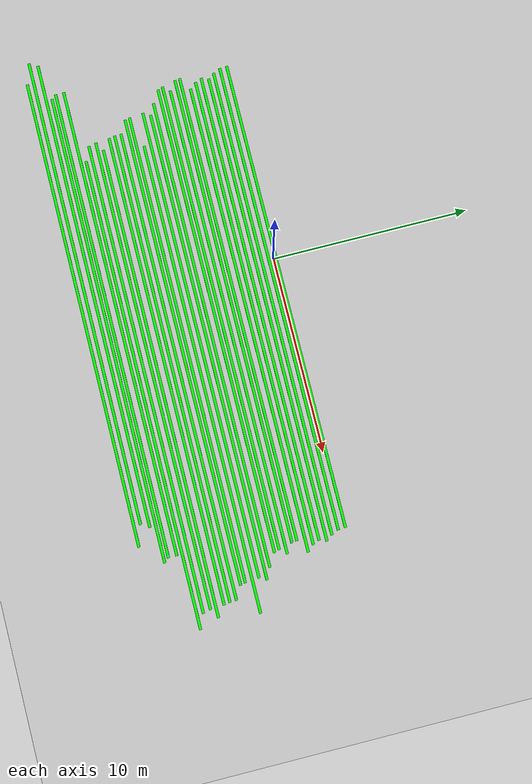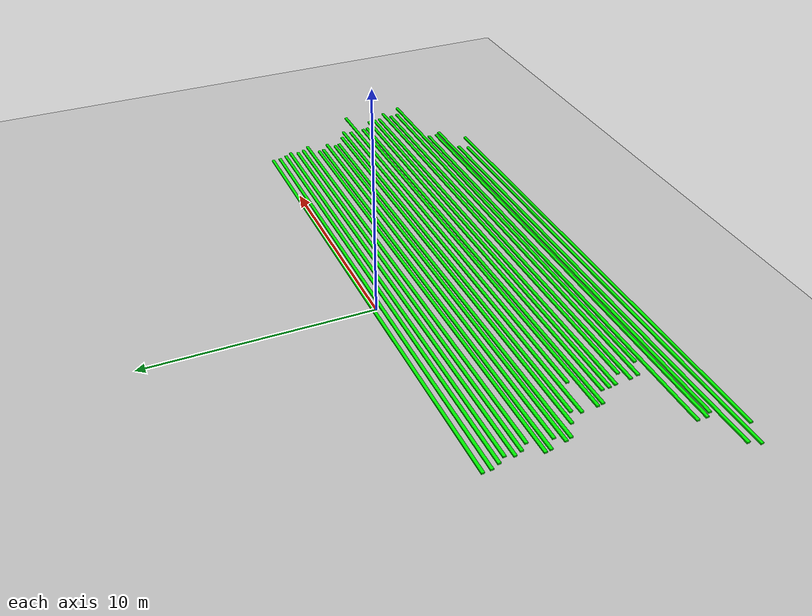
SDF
<sdf version="1.7">
 <world name="default">
  <light name="sun" type="directional">
   <pose>0 0 10 0 -0 0</pose>
   <diffuse>0.8 0.8 0.8 1</diffuse>
   <specular>0.2 0.2 0.2 1</specular>
   <attenuation>
    <range>1000</range>
    <constant>0.9</constant>
    <linear>0.01</linear>
    <quadratic>0.001</quadratic>
   </attenuation>
   <direction>-0.5 0.1 -0.9</direction>
   <spot><inner_angle>0</inner_angle><outer_angle>0</outer_angle><falloff>0</falloff></spot>
  </light>
  <model name="ground_plane">
   <static>1</static>
   <link name="link">
    <collision name="collision">
     <geometry><plane><normal>0 0 1</normal><size>100 100</size></plane></geometry>
     <surface>
      <contact><collide_bitmask>65535</collide_bitmask></contact>
      <friction><ode><mu>100</mu><mu2>50</mu2></ode></friction>
     </surface>
    </collision>
    <visual name="visual">
     <cast_shadows>0</cast_shadows>
     <geometry><plane><normal>0 0 1</normal><size>100 100</size></plane></geometry>
     <material>
      <script><uri>file://media/materials/scripts/gazebo.material</uri><name>Gazebo/Grey</name></script>
     </material>
    </visual>
   </link>
  </model>
  <gravity>0 0 -9.8</gravity>
  <magnetic_field>6e-06 2.3e-05 -4.2e-05</magnetic_field>
  <atmosphere type="adiabatic"/>
  <physics type="ode">
   <max_step_size>0.001</max_step_size>
   <real_time_factor>1</real_time_factor>
   <real_time_update_rate>1000</real_time_update_rate>
  </physics>
  <scene><ambient>0.4 0.4 0.4 1</ambient><background>0.7 0.7 0.7 1</background><shadows>1</shadows></scene>
  <spherical_coordinates>
   <surface_model>EARTH_WGS84</surface_model>
   <latitude_deg>0</latitude_deg>
   <longitude_deg>0</longitude_deg>
   <elevation>0</elevation>
   <heading_deg>0</heading_deg>
  </spherical_coordinates>
  <model name="one_crop_row">
   <link name="link_0">
    <inertial>
     <mass>9.98</mass>
     <inertia>
      <ixx>0.166667</ixx>
      <ixy>0</ixy>
      <ixz>0</ixz>
      <iyy>0.166667</iyy>
      <iyz>0</iyz>
      <izz>0.166667</izz>
     </inertia>
    </inertial>
    <visual name="visual">
     <geometry><mesh><uri>/home/devesh/one_crop_row.stl</uri><scale>1 1 1</scale></mesh></geometry>
     <material>
      <lighting>1</lighting>
      <script><uri>file://media/materials/scripts/gazebo.material</uri><name>Gazebo/Grey</name></script>
      <shader type="pixel"><normal_map>__default__</normal_map></shader>
      <ambient>0 1 0 0</ambient>
      <diffuse>0 1 0 0</diffuse>
      <specular>0 1 0 0</specular>
      <emissive>0 0 0 1</emissive>
     </material>
    </visual>
    <collision name="collision">
     <geometry><mesh><uri>/home/devesh/one_crop_row.stl</uri><scale>1 1 1</scale></mesh></geometry>
     <surface>
      <friction>
       <ode><mu>1</mu><mu2>1</mu2><fdir1>0 0 0</fdir1><slip1>0</slip1><slip2>0</slip2></ode>
       <torsional>
        <coefficient>1</coefficient>
        <patch_radius>0</patch_radius>
        <surface_radius>0</surface_radius>
        <use_patch_radius>1</use_patch_radius>
        <ode><slip>0</slip></ode>
       </torsional>
      </friction>
      <bounce><restitution_coefficient>0</restitution_coefficient><threshold>1e+06</threshold></bounce>
      <contact>
       <collide_without_contact>0</collide_without_contact>
       <collide_without_contact_bitmask>1</collide_without_contact_bitmask>
       <collide_bitmask>1</collide_bitmask>
       <ode>
        <soft_cfm>0</soft_cfm>
        <soft_erp>0.2</soft_erp>
        <kp>1e+13</kp>
        <kd>1</kd>
        <max_vel>0.01</max_vel>
        <min_depth>0</min_depth>
       </ode>
       <bullet>
        <split_impulse>1</split_impulse>
        <split_impulse_penetration_threshold>-0.01</split_impulse_penetration_threshold>
        <soft_cfm>0</soft_cfm>
        <soft_erp>0.2</soft_erp>
        <kp>1e+13</kp>
        <kd>1</kd>
       </bullet>
      </contact>
     </surface>
    </collision>
   </link>
   <static>0</static>
   <pose>-0.146054 0.114971 0.015873 -0.021759 0 0.000192</pose>
  </model>
  <model name="one_crop_row_clone">
   <link name="link_0">
    <inertial>
     <mass>9.98</mass>
     <inertia>
      <ixx>0.166667</ixx>
      <ixy>0</ixy>
      <ixz>0</ixz>
      <iyy>0.166667</iyy>
      <iyz>0</iyz>
      <izz>0.166667</izz>
     </inertia>
    </inertial>
    <visual name="visual">
     <geometry><mesh><uri>/home/devesh/one_crop_row.stl</uri><scale>1 1 1</scale></mesh></geometry>
     <material>
      <lighting>1</lighting>
      <script><uri>file://media/materials/scripts/gazebo.material</uri><name>Gazebo/Grey</name></script>
      <shader type="pixel"><normal_map>__default__</normal_map></shader>
      <ambient>0 1 0 0</ambient>
      <diffuse>0 1 0 0</diffuse>
      <specular>0 1 0 0</specular>
      <emissive>0 0 0 1</emissive>
     </material>
    </visual>
    <collision name="collision">
     <geometry><mesh><uri>/home/devesh/one_crop_row.stl</uri><scale>1 1 1</scale></mesh></geometry>
     <surface>
      <friction>
       <ode><mu>1</mu><mu2>1</mu2><fdir1>0 0 0</fdir1><slip1>0</slip1><slip2>0</slip2></ode>
       <torsional>
        <coefficient>1</coefficient>
        <patch_radius>0</patch_radius>
        <surface_radius>0</surface_radius>
        <use_patch_radius>1</use_patch_radius>
        <ode><slip>0</slip></ode>
       </torsional>
      </friction>
      <bounce><restitution_coefficient>0</restitution_coefficient><threshold>1e+06</threshold></bounce>
      <contact>
       <collide_without_contact>0</collide_without_contact>
       <collide_without_contact_bitmask>1</collide_without_contact_bitmask>
       <collide_bitmask>1</collide_bitmask>
       <ode>
        <soft_cfm>0</soft_cfm>
        <soft_erp>0.2</soft_erp>
        <kp>1e+13</kp>
        <kd>1</kd>
        <max_vel>0.01</max_vel>
        <min_depth>0</min_depth>
       </ode>
       <bullet>
        <split_impulse>1</split_impulse>
        <split_impulse_penetration_threshold>-0.01</split_impulse_penetration_threshold>
        <soft_cfm>0</soft_cfm>
        <soft_erp>0.2</soft_erp>
        <kp>1e+13</kp>
        <kd>1</kd>
       </bullet>
      </contact>
     </surface>
    </collision>
   </link>
   <static>0</static>
   <pose>0.274892 -0.931708 0.015872 -0.022045 -0 0.000192</pose>
  </model>
  <model name="one_crop_row_clone_0">
   <link name="link_0">
    <inertial>
     <mass>9.98</mass>
     <inertia>
      <ixx>0.166667</ixx>
      <ixy>0</ixy>
      <ixz>0</ixz>
      <iyy>0.166667</iyy>
      <iyz>0</iyz>
      <izz>0.166667</izz>
     </inertia>
    </inertial>
    <visual name="visual">
     <geometry><mesh><uri>/home/devesh/one_crop_row.stl</uri><scale>1 1 1</scale></mesh></geometry>
     <material>
      <lighting>1</lighting>
      <script><uri>file://media/materials/scripts/gazebo.material</uri><name>Gazebo/Grey</name></script>
      <shader type="pixel"><normal_map>__default__</normal_map></shader>
      <ambient>0 1 0 0</ambient>
      <diffuse>0 1 0 0</diffuse>
      <specular>0 1 0 0</specular>
      <emissive>0 0 0 1</emissive>
     </material>
    </visual>
    <collision name="collision">
     <geometry><mesh><uri>/home/devesh/one_crop_row.stl</uri><scale>1 1 1</scale></mesh></geometry>
     <surface>
      <friction>
       <ode><mu>1</mu><mu2>1</mu2><fdir1>0 0 0</fdir1><slip1>0</slip1><slip2>0</slip2></ode>
       <torsional>
        <coefficient>1</coefficient>
        <patch_radius>0</patch_radius>
        <surface_radius>0</surface_radius>
        <use_patch_radius>1</use_patch_radius>
        <ode><slip>0</slip></ode>
       </torsional>
      </friction>
      <bounce><restitution_coefficient>0</restitution_coefficient><threshold>1e+06</threshold></bounce>
      <contact>
       <collide_without_contact>0</collide_without_contact>
       <collide_without_contact_bitmask>1</collide_without_contact_bitmask>
       <collide_bitmask>1</collide_bitmask>
       <ode>
        <soft_cfm>0</soft_cfm>
        <soft_erp>0.2</soft_erp>
        <kp>1e+13</kp>
        <kd>1</kd>
        <max_vel>0.01</max_vel>
        <min_depth>0</min_depth>
       </ode>
       <bullet>
        <split_impulse>1</split_impulse>
        <split_impulse_penetration_threshold>-0.01</split_impulse_penetration_threshold>
        <soft_cfm>0</soft_cfm>
        <soft_erp>0.2</soft_erp>
        <kp>1e+13</kp>
        <kd>1</kd>
       </bullet>
      </contact>
     </surface>
    </collision>
   </link>
   <static>0</static>
   <pose>-0.112666 -0.25225 0.015872 -0.022063 -0 0.000192</pose>
  </model>
  <model name="one_crop_row_clone_1">
   <link name="link_0">
    <inertial>
     <mass>9.98</mass>
     <inertia>
      <ixx>0.166667</ixx>
      <ixy>0</ixy>
      <ixz>0</ixz>
      <iyy>0.166667</iyy>
      <iyz>0</iyz>
      <izz>0.166667</izz>
     </inertia>
    </inertial>
    <visual name="visual">
     <geometry><mesh><uri>/home/devesh/one_crop_row.stl</uri><scale>1 1 1</scale></mesh></geometry>
     <material>
      <lighting>1</lighting>
      <script><uri>file://media/materials/scripts/gazebo.material</uri><name>Gazebo/Grey</name></script>
      <shader type="pixel"><normal_map>__default__</normal_map></shader>
      <ambient>0 1 0 0</ambient>
      <diffuse>0 1 0 0</diffuse>
      <specular>0 1 0 0</specular>
      <emissive>0 0 0 1</emissive>
     </material>
    </visual>
    <collision name="collision">
     <geometry><mesh><uri>/home/devesh/one_crop_row.stl</uri><scale>1 1 1</scale></mesh></geometry>
     <surface>
      <friction>
       <ode><mu>1</mu><mu2>1</mu2><fdir1>0 0 0</fdir1><slip1>0</slip1><slip2>0</slip2></ode>
       <torsional>
        <coefficient>1</coefficient>
        <patch_radius>0</patch_radius>
        <surface_radius>0</surface_radius>
        <use_patch_radius>1</use_patch_radius>
        <ode><slip>0</slip></ode>
       </torsional>
      </friction>
      <bounce><restitution_coefficient>0</restitution_coefficient><threshold>1e+06</threshold></bounce>
      <contact>
       <collide_without_contact>0</collide_without_contact>
       <collide_without_contact_bitmask>1</collide_without_contact_bitmask>
       <collide_bitmask>1</collide_bitmask>
       <ode>
        <soft_cfm>0</soft_cfm>
        <soft_erp>0.2</soft_erp>
        <kp>1e+13</kp>
        <kd>1</kd>
        <max_vel>0.01</max_vel>
        <min_depth>0</min_depth>
       </ode>
       <bullet>
        <split_impulse>1</split_impulse>
        <split_impulse_penetration_threshold>-0.01</split_impulse_penetration_threshold>
        <soft_cfm>0</soft_cfm>
        <soft_erp>0.2</soft_erp>
        <kp>1e+13</kp>
        <kd>1</kd>
       </bullet>
      </contact>
     </surface>
    </collision>
   </link>
   <static>0</static>
   <pose>0.046398 -0.61756 0.015874 -0.021701 0 0.000192</pose>
  </model>
  <model name="one_crop_row_clone_2">
   <link name="link_0">
    <inertial>
     <mass>9.98</mass>
     <inertia>
      <ixx>0.166667</ixx>
      <ixy>0</ixy>
      <ixz>0</ixz>
      <iyy>0.166667</iyy>
      <iyz>0</iyz>
      <izz>0.166667</izz>
     </inertia>
    </inertial>
    <visual name="visual">
     <geometry><mesh><uri>/home/devesh/one_crop_row.stl</uri><scale>1 1 1</scale></mesh></geometry>
     <material>
      <lighting>1</lighting>
      <script><uri>file://media/materials/scripts/gazebo.material</uri><name>Gazebo/Grey</name></script>
      <shader type="pixel"><normal_map>__default__</normal_map></shader>
      <ambient>0 1 0 0</ambient>
      <diffuse>0 1 0 0</diffuse>
      <specular>0 1 0 0</specular>
      <emissive>0 0 0 1</emissive>
     </material>
    </visual>
    <collision name="collision">
     <geometry><mesh><uri>/home/devesh/one_crop_row.stl</uri><scale>1 1 1</scale></mesh></geometry>
     <surface>
      <friction>
       <ode><mu>1</mu><mu2>1</mu2><fdir1>0 0 0</fdir1><slip1>0</slip1><slip2>0</slip2></ode>
       <torsional>
        <coefficient>1</coefficient>
        <patch_radius>0</patch_radius>
        <surface_radius>0</surface_radius>
        <use_patch_radius>1</use_patch_radius>
        <ode><slip>0</slip></ode>
       </torsional>
      </friction>
      <bounce><restitution_coefficient>0</restitution_coefficient><threshold>1e+06</threshold></bounce>
      <contact>
       <collide_without_contact>0</collide_without_contact>
       <collide_without_contact_bitmask>1</collide_without_contact_bitmask>
       <collide_bitmask>1</collide_bitmask>
       <ode>
        <soft_cfm>0</soft_cfm>
        <soft_erp>0.2</soft_erp>
        <kp>1e+13</kp>
        <kd>1</kd>
        <max_vel>0.01</max_vel>
        <min_depth>0</min_depth>
       </ode>
       <bullet>
        <split_impulse>1</split_impulse>
        <split_impulse_penetration_threshold>-0.01</split_impulse_penetration_threshold>
        <soft_cfm>0</soft_cfm>
        <soft_erp>0.2</soft_erp>
        <kp>1e+13</kp>
        <kd>1</kd>
       </bullet>
      </contact>
     </surface>
    </collision>
   </link>
   <static>0</static>
   <pose>0.564726 -1.95281 0.015872 -0.022058 -0 0.000192</pose>
  </model>
  <model name="one_crop_row_clone_3">
   <link name="link_0">
    <inertial>
     <mass>9.98</mass>
     <inertia>
      <ixx>0.166667</ixx>
      <ixy>0</ixy>
      <ixz>0</ixz>
      <iyy>0.166667</iyy>
      <iyz>0</iyz>
      <izz>0.166667</izz>
     </inertia>
    </inertial>
    <visual name="visual">
     <geometry><mesh><uri>/home/devesh/one_crop_row.stl</uri><scale>1 1 1</scale></mesh></geometry>
     <material>
      <lighting>1</lighting>
      <script><uri>file://media/materials/scripts/gazebo.material</uri><name>Gazebo/Grey</name></script>
      <shader type="pixel"><normal_map>__default__</normal_map></shader>
      <ambient>0 1 0 0</ambient>
      <diffuse>0 1 0 0</diffuse>
      <specular>0 1 0 0</specular>
      <emissive>0 0 0 1</emissive>
     </material>
    </visual>
    <collision name="collision">
     <geometry><mesh><uri>/home/devesh/one_crop_row.stl</uri><scale>1 1 1</scale></mesh></geometry>
     <surface>
      <friction>
       <ode><mu>1</mu><mu2>1</mu2><fdir1>0 0 0</fdir1><slip1>0</slip1><slip2>0</slip2></ode>
       <torsional>
        <coefficient>1</coefficient>
        <patch_radius>0</patch_radius>
        <surface_radius>0</surface_radius>
        <use_patch_radius>1</use_patch_radius>
        <ode><slip>0</slip></ode>
       </torsional>
      </friction>
      <bounce><restitution_coefficient>0</restitution_coefficient><threshold>1e+06</threshold></bounce>
      <contact>
       <collide_without_contact>0</collide_without_contact>
       <collide_without_contact_bitmask>1</collide_without_contact_bitmask>
       <collide_bitmask>1</collide_bitmask>
       <ode>
        <soft_cfm>0</soft_cfm>
        <soft_erp>0.2</soft_erp>
        <kp>1e+13</kp>
        <kd>1</kd>
        <max_vel>0.01</max_vel>
        <min_depth>0</min_depth>
       </ode>
       <bullet>
        <split_impulse>1</split_impulse>
        <split_impulse_penetration_threshold>-0.01</split_impulse_penetration_threshold>
        <soft_cfm>0</soft_cfm>
        <soft_erp>0.2</soft_erp>
        <kp>1e+13</kp>
        <kd>1</kd>
       </bullet>
      </contact>
     </surface>
    </collision>
   </link>
   <static>0</static>
   <pose>0.149362 -1.29673 0.015866 -0.022111 -1e-06 0.000192</pose>
  </model>
  <model name="one_crop_row_clone_4">
   <link name="link_0">
    <inertial>
     <mass>9.98</mass>
     <inertia>
      <ixx>0.166667</ixx>
      <ixy>0</ixy>
      <ixz>0</ixz>
      <iyy>0.166667</iyy>
      <iyz>0</iyz>
      <izz>0.166667</izz>
     </inertia>
    </inertial>
    <visual name="visual">
     <geometry><mesh><uri>/home/devesh/one_crop_row.stl</uri><scale>1 1 1</scale></mesh></geometry>
     <material>
      <lighting>1</lighting>
      <script><uri>file://media/materials/scripts/gazebo.material</uri><name>Gazebo/Grey</name></script>
      <shader type="pixel"><normal_map>__default__</normal_map></shader>
      <ambient>0 1 0 0</ambient>
      <diffuse>0 1 0 0</diffuse>
      <specular>0 1 0 0</specular>
      <emissive>0 0 0 1</emissive>
     </material>
    </visual>
    <collision name="collision">
     <geometry><mesh><uri>/home/devesh/one_crop_row.stl</uri><scale>1 1 1</scale></mesh></geometry>
     <surface>
      <friction>
       <ode><mu>1</mu><mu2>1</mu2><fdir1>0 0 0</fdir1><slip1>0</slip1><slip2>0</slip2></ode>
       <torsional>
        <coefficient>1</coefficient>
        <patch_radius>0</patch_radius>
        <surface_radius>0</surface_radius>
        <use_patch_radius>1</use_patch_radius>
        <ode><slip>0</slip></ode>
       </torsional>
      </friction>
      <bounce><restitution_coefficient>0</restitution_coefficient><threshold>1e+06</threshold></bounce>
      <contact>
       <collide_without_contact>0</collide_without_contact>
       <collide_without_contact_bitmask>1</collide_without_contact_bitmask>
       <collide_bitmask>1</collide_bitmask>
       <ode>
        <soft_cfm>0</soft_cfm>
        <soft_erp>0.2</soft_erp>
        <kp>1e+13</kp>
        <kd>1</kd>
        <max_vel>0.01</max_vel>
        <min_depth>0</min_depth>
       </ode>
       <bullet>
        <split_impulse>1</split_impulse>
        <split_impulse_penetration_threshold>-0.01</split_impulse_penetration_threshold>
        <soft_cfm>0</soft_cfm>
        <soft_erp>0.2</soft_erp>
        <kp>1e+13</kp>
        <kd>1</kd>
       </bullet>
      </contact>
     </surface>
    </collision>
   </link>
   <static>0</static>
   <pose>0.286169 -1.62393 0.015863 -0.022038 -0 0.000192</pose>
  </model>
  <model name="one_crop_row_clone_5">
   <link name="link_0">
    <inertial>
     <mass>9.98</mass>
     <inertia>
      <ixx>0.166667</ixx>
      <ixy>0</ixy>
      <ixz>0</ixz>
      <iyy>0.166667</iyy>
      <iyz>0</iyz>
      <izz>0.166667</izz>
     </inertia>
    </inertial>
    <visual name="visual">
     <geometry><mesh><uri>/home/devesh/one_crop_row.stl</uri><scale>1 1 1</scale></mesh></geometry>
     <material>
      <lighting>1</lighting>
      <script><uri>file://media/materials/scripts/gazebo.material</uri><name>Gazebo/Grey</name></script>
      <shader type="pixel"><normal_map>__default__</normal_map></shader>
      <ambient>0 1 0 0</ambient>
      <diffuse>0 1 0 0</diffuse>
      <specular>0 1 0 0</specular>
      <emissive>0 0 0 1</emissive>
     </material>
    </visual>
    <collision name="collision">
     <geometry><mesh><uri>/home/devesh/one_crop_row.stl</uri><scale>1 1 1</scale></mesh></geometry>
     <surface>
      <friction>
       <ode><mu>1</mu><mu2>1</mu2><fdir1>0 0 0</fdir1><slip1>0</slip1><slip2>0</slip2></ode>
       <torsional>
        <coefficient>1</coefficient>
        <patch_radius>0</patch_radius>
        <surface_radius>0</surface_radius>
        <use_patch_radius>1</use_patch_radius>
        <ode><slip>0</slip></ode>
       </torsional>
      </friction>
      <bounce><restitution_coefficient>0</restitution_coefficient><threshold>1e+06</threshold></bounce>
      <contact>
       <collide_without_contact>0</collide_without_contact>
       <collide_without_contact_bitmask>1</collide_without_contact_bitmask>
       <collide_bitmask>1</collide_bitmask>
       <ode>
        <soft_cfm>0</soft_cfm>
        <soft_erp>0.2</soft_erp>
        <kp>1e+13</kp>
        <kd>1</kd>
        <max_vel>0.01</max_vel>
        <min_depth>0</min_depth>
       </ode>
       <bullet>
        <split_impulse>1</split_impulse>
        <split_impulse_penetration_threshold>-0.01</split_impulse_penetration_threshold>
        <soft_cfm>0</soft_cfm>
        <soft_erp>0.2</soft_erp>
        <kp>1e+13</kp>
        <kd>1</kd>
       </bullet>
      </contact>
     </surface>
    </collision>
   </link>
   <static>0</static>
   <pose>0.396656 -2.97327 0.015873 -0.021941 0 0.000192</pose>
  </model>
  <model name="one_crop_row_clone_6">
   <link name="link_0">
    <inertial>
     <mass>9.98</mass>
     <inertia>
      <ixx>0.166667</ixx>
      <ixy>0</ixy>
      <ixz>0</ixz>
      <iyy>0.166667</iyy>
      <iyz>0</iyz>
      <izz>0.166667</izz>
     </inertia>
    </inertial>
    <visual name="visual">
     <geometry><mesh><uri>/home/devesh/one_crop_row.stl</uri><scale>1 1 1</scale></mesh></geometry>
     <material>
      <lighting>1</lighting>
      <script><uri>file://media/materials/scripts/gazebo.material</uri><name>Gazebo/Grey</name></script>
      <shader type="pixel"><normal_map>__default__</normal_map></shader>
      <ambient>0 1 0 0</ambient>
      <diffuse>0 1 0 0</diffuse>
      <specular>0 1 0 0</specular>
      <emissive>0 0 0 1</emissive>
     </material>
    </visual>
    <collision name="collision">
     <geometry><mesh><uri>/home/devesh/one_crop_row.stl</uri><scale>1 1 1</scale></mesh></geometry>
     <surface>
      <friction>
       <ode><mu>1</mu><mu2>1</mu2><fdir1>0 0 0</fdir1><slip1>0</slip1><slip2>0</slip2></ode>
       <torsional>
        <coefficient>1</coefficient>
        <patch_radius>0</patch_radius>
        <surface_radius>0</surface_radius>
        <use_patch_radius>1</use_patch_radius>
        <ode><slip>0</slip></ode>
       </torsional>
      </friction>
      <bounce><restitution_coefficient>0</restitution_coefficient><threshold>1e+06</threshold></bounce>
      <contact>
       <collide_without_contact>0</collide_without_contact>
       <collide_without_contact_bitmask>1</collide_without_contact_bitmask>
       <collide_bitmask>1</collide_bitmask>
       <ode>
        <soft_cfm>0</soft_cfm>
        <soft_erp>0.2</soft_erp>
        <kp>1e+13</kp>
        <kd>1</kd>
        <max_vel>0.01</max_vel>
        <min_depth>0</min_depth>
       </ode>
       <bullet>
        <split_impulse>1</split_impulse>
        <split_impulse_penetration_threshold>-0.01</split_impulse_penetration_threshold>
        <soft_cfm>0</soft_cfm>
        <soft_erp>0.2</soft_erp>
        <kp>1e+13</kp>
        <kd>1</kd>
       </bullet>
      </contact>
     </surface>
    </collision>
   </link>
   <static>0</static>
   <pose>-0.107863 -2.36178 0.015871 -0.022082 -3e-06 0.000192</pose>
  </model>
  <model name="one_crop_row_clone_7">
   <link name="link_0">
    <inertial>
     <mass>9.98</mass>
     <inertia>
      <ixx>0.166667</ixx>
      <ixy>0</ixy>
      <ixz>0</ixz>
      <iyy>0.166667</iyy>
      <iyz>0</iyz>
      <izz>0.166667</izz>
     </inertia>
    </inertial>
    <visual name="visual">
     <geometry><mesh><uri>/home/devesh/one_crop_row.stl</uri><scale>1 1 1</scale></mesh></geometry>
     <material>
      <lighting>1</lighting>
      <script><uri>file://media/materials/scripts/gazebo.material</uri><name>Gazebo/Grey</name></script>
      <shader type="pixel"><normal_map>__default__</normal_map></shader>
      <ambient>0 1 0 0</ambient>
      <diffuse>0 1 0 0</diffuse>
      <specular>0 1 0 0</specular>
      <emissive>0 0 0 1</emissive>
     </material>
    </visual>
    <collision name="collision">
     <geometry><mesh><uri>/home/devesh/one_crop_row.stl</uri><scale>1 1 1</scale></mesh></geometry>
     <surface>
      <friction>
       <ode><mu>1</mu><mu2>1</mu2><fdir1>0 0 0</fdir1><slip1>0</slip1><slip2>0</slip2></ode>
       <torsional>
        <coefficient>1</coefficient>
        <patch_radius>0</patch_radius>
        <surface_radius>0</surface_radius>
        <use_patch_radius>1</use_patch_radius>
        <ode><slip>0</slip></ode>
       </torsional>
      </friction>
      <bounce><restitution_coefficient>0</restitution_coefficient><threshold>1e+06</threshold></bounce>
      <contact>
       <collide_without_contact>0</collide_without_contact>
       <collide_without_contact_bitmask>1</collide_without_contact_bitmask>
       <collide_bitmask>1</collide_bitmask>
       <ode>
        <soft_cfm>0</soft_cfm>
        <soft_erp>0.2</soft_erp>
        <kp>1e+13</kp>
        <kd>1</kd>
        <max_vel>0.01</max_vel>
        <min_depth>0</min_depth>
       </ode>
       <bullet>
        <split_impulse>1</split_impulse>
        <split_impulse_penetration_threshold>-0.01</split_impulse_penetration_threshold>
        <soft_cfm>0</soft_cfm>
        <soft_erp>0.2</soft_erp>
        <kp>1e+13</kp>
        <kd>1</kd>
       </bullet>
      </contact>
     </surface>
    </collision>
   </link>
   <static>0</static>
   <pose>-0.066521 -2.61551 0.015872 -0.022063 -0 0.000192</pose>
  </model>
  <model name="one_crop_row_clone_8">
   <link name="link_0">
    <inertial>
     <mass>9.98</mass>
     <inertia>
      <ixx>0.166667</ixx>
      <ixy>0</ixy>
      <ixz>0</ixz>
      <iyy>0.166667</iyy>
      <iyz>0</iyz>
      <izz>0.166667</izz>
     </inertia>
    </inertial>
    <visual name="visual">
     <geometry><mesh><uri>/home/devesh/one_crop_row.stl</uri><scale>1 1 1</scale></mesh></geometry>
     <material>
      <lighting>1</lighting>
      <script><uri>file://media/materials/scripts/gazebo.material</uri><name>Gazebo/Grey</name></script>
      <shader type="pixel"><normal_map>__default__</normal_map></shader>
      <ambient>0 1 0 0</ambient>
      <diffuse>0 1 0 0</diffuse>
      <specular>0 1 0 0</specular>
      <emissive>0 0 0 1</emissive>
     </material>
    </visual>
    <collision name="collision">
     <geometry><mesh><uri>/home/devesh/one_crop_row.stl</uri><scale>1 1 1</scale></mesh></geometry>
     <surface>
      <friction>
       <ode><mu>1</mu><mu2>1</mu2><fdir1>0 0 0</fdir1><slip1>0</slip1><slip2>0</slip2></ode>
       <torsional>
        <coefficient>1</coefficient>
        <patch_radius>0</patch_radius>
        <surface_radius>0</surface_radius>
        <use_patch_radius>1</use_patch_radius>
        <ode><slip>0</slip></ode>
       </torsional>
      </friction>
      <bounce><restitution_coefficient>0</restitution_coefficient><threshold>1e+06</threshold></bounce>
      <contact>
       <collide_without_contact>0</collide_without_contact>
       <collide_without_contact_bitmask>1</collide_without_contact_bitmask>
       <collide_bitmask>1</collide_bitmask>
       <ode>
        <soft_cfm>0</soft_cfm>
        <soft_erp>0.2</soft_erp>
        <kp>1e+13</kp>
        <kd>1</kd>
        <max_vel>0.01</max_vel>
        <min_depth>0</min_depth>
       </ode>
       <bullet>
        <split_impulse>1</split_impulse>
        <split_impulse_penetration_threshold>-0.01</split_impulse_penetration_threshold>
        <soft_cfm>0</soft_cfm>
        <soft_erp>0.2</soft_erp>
        <kp>1e+13</kp>
        <kd>1</kd>
       </bullet>
      </contact>
     </surface>
    </collision>
   </link>
   <static>0</static>
   <pose>0.829495 -3.96048 0.015869 -0.022102 1e-06 0.000192</pose>
  </model>
  <model name="one_crop_row_clone_9">
   <link name="link_0">
    <inertial>
     <mass>9.98</mass>
     <inertia>
      <ixx>0.166667</ixx>
      <ixy>0</ixy>
      <ixz>0</ixz>
      <iyy>0.166667</iyy>
      <iyz>0</iyz>
      <izz>0.166667</izz>
     </inertia>
    </inertial>
    <visual name="visual">
     <geometry><mesh><uri>/home/devesh/one_crop_row.stl</uri><scale>1 1 1</scale></mesh></geometry>
     <material>
      <lighting>1</lighting>
      <script><uri>file://media/materials/scripts/gazebo.material</uri><name>Gazebo/Grey</name></script>
      <shader type="pixel"><normal_map>__default__</normal_map></shader>
      <ambient>0 1 0 0</ambient>
      <diffuse>0 1 0 0</diffuse>
      <specular>0 1 0 0</specular>
      <emissive>0 0 0 1</emissive>
     </material>
    </visual>
    <collision name="collision">
     <geometry><mesh><uri>/home/devesh/one_crop_row.stl</uri><scale>1 1 1</scale></mesh></geometry>
     <surface>
      <friction>
       <ode><mu>1</mu><mu2>1</mu2><fdir1>0 0 0</fdir1><slip1>0</slip1><slip2>0</slip2></ode>
       <torsional>
        <coefficient>1</coefficient>
        <patch_radius>0</patch_radius>
        <surface_radius>0</surface_radius>
        <use_patch_radius>1</use_patch_radius>
        <ode><slip>0</slip></ode>
       </torsional>
      </friction>
      <bounce><restitution_coefficient>0</restitution_coefficient><threshold>1e+06</threshold></bounce>
      <contact>
       <collide_without_contact>0</collide_without_contact>
       <collide_without_contact_bitmask>1</collide_without_contact_bitmask>
       <collide_bitmask>1</collide_bitmask>
       <ode>
        <soft_cfm>0</soft_cfm>
        <soft_erp>0.2</soft_erp>
        <kp>1e+13</kp>
        <kd>1</kd>
        <max_vel>0.01</max_vel>
        <min_depth>0</min_depth>
       </ode>
       <bullet>
        <split_impulse>1</split_impulse>
        <split_impulse_penetration_threshold>-0.01</split_impulse_penetration_threshold>
        <soft_cfm>0</soft_cfm>
        <soft_erp>0.2</soft_erp>
        <kp>1e+13</kp>
        <kd>1</kd>
       </bullet>
      </contact>
     </surface>
    </collision>
   </link>
   <static>0</static>
   <pose>0.104402 -3.31136 0.015873 -0.021732 -0 0.000192</pose>
  </model>
  <model name="one_crop_row_clone_10">
   <link name="link_0">
    <inertial>
     <mass>9.98</mass>
     <inertia>
      <ixx>0.166667</ixx>
      <ixy>0</ixy>
      <ixz>0</ixz>
      <iyy>0.166667</iyy>
      <iyz>0</iyz>
      <izz>0.166667</izz>
     </inertia>
    </inertial>
    <visual name="visual">
     <geometry><mesh><uri>/home/devesh/one_crop_row.stl</uri><scale>1 1 1</scale></mesh></geometry>
     <material>
      <lighting>1</lighting>
      <script><uri>file://media/materials/scripts/gazebo.material</uri><name>Gazebo/Grey</name></script>
      <shader type="pixel"><normal_map>__default__</normal_map></shader>
      <ambient>0 1 0 0</ambient>
      <diffuse>0 1 0 0</diffuse>
      <specular>0 1 0 0</specular>
      <emissive>0 0 0 1</emissive>
     </material>
    </visual>
    <collision name="collision">
     <geometry><mesh><uri>/home/devesh/one_crop_row.stl</uri><scale>1 1 1</scale></mesh></geometry>
     <surface>
      <friction>
       <ode><mu>1</mu><mu2>1</mu2><fdir1>0 0 0</fdir1><slip1>0</slip1><slip2>0</slip2></ode>
       <torsional>
        <coefficient>1</coefficient>
        <patch_radius>0</patch_radius>
        <surface_radius>0</surface_radius>
        <use_patch_radius>1</use_patch_radius>
        <ode><slip>0</slip></ode>
       </torsional>
      </friction>
      <bounce><restitution_coefficient>0</restitution_coefficient><threshold>1e+06</threshold></bounce>
      <contact>
       <collide_without_contact>0</collide_without_contact>
       <collide_without_contact_bitmask>1</collide_without_contact_bitmask>
       <collide_bitmask>1</collide_bitmask>
       <ode>
        <soft_cfm>0</soft_cfm>
        <soft_erp>0.2</soft_erp>
        <kp>1e+13</kp>
        <kd>1</kd>
        <max_vel>0.01</max_vel>
        <min_depth>0</min_depth>
       </ode>
       <bullet>
        <split_impulse>1</split_impulse>
        <split_impulse_penetration_threshold>-0.01</split_impulse_penetration_threshold>
        <soft_cfm>0</soft_cfm>
        <soft_erp>0.2</soft_erp>
        <kp>1e+13</kp>
        <kd>1</kd>
       </bullet>
      </contact>
     </surface>
    </collision>
   </link>
   <static>0</static>
   <pose>0.196506 -3.56718 0.015873 -0.021966 -0 0.000192</pose>
  </model>
  <model name="one_crop_row_clone_11">
   <link name="link_0">
    <inertial>
     <mass>9.98</mass>
     <inertia>
      <ixx>0.166667</ixx>
      <ixy>0</ixy>
      <ixz>0</ixz>
      <iyy>0.166667</iyy>
      <iyz>0</iyz>
      <izz>0.166667</izz>
     </inertia>
    </inertial>
    <visual name="visual">
     <geometry><mesh><uri>/home/devesh/one_crop_row.stl</uri><scale>1 1 1</scale></mesh></geometry>
     <material>
      <lighting>1</lighting>
      <script><uri>file://media/materials/scripts/gazebo.material</uri><name>Gazebo/Grey</name></script>
      <shader type="pixel"><normal_map>__default__</normal_map></shader>
      <ambient>0 1 0 0</ambient>
      <diffuse>0 1 0 0</diffuse>
      <specular>0 1 0 0</specular>
      <emissive>0 0 0 1</emissive>
     </material>
    </visual>
    <collision name="collision">
     <geometry><mesh><uri>/home/devesh/one_crop_row.stl</uri><scale>1 1 1</scale></mesh></geometry>
     <surface>
      <friction>
       <ode><mu>1</mu><mu2>1</mu2><fdir1>0 0 0</fdir1><slip1>0</slip1><slip2>0</slip2></ode>
       <torsional>
        <coefficient>1</coefficient>
        <patch_radius>0</patch_radius>
        <surface_radius>0</surface_radius>
        <use_patch_radius>1</use_patch_radius>
        <ode><slip>0</slip></ode>
       </torsional>
      </friction>
      <bounce><restitution_coefficient>0</restitution_coefficient><threshold>1e+06</threshold></bounce>
      <contact>
       <collide_without_contact>0</collide_without_contact>
       <collide_without_contact_bitmask>1</collide_without_contact_bitmask>
       <collide_bitmask>1</collide_bitmask>
       <ode>
        <soft_cfm>0</soft_cfm>
        <soft_erp>0.2</soft_erp>
        <kp>1e+13</kp>
        <kd>1</kd>
        <max_vel>0.01</max_vel>
        <min_depth>0</min_depth>
       </ode>
       <bullet>
        <split_impulse>1</split_impulse>
        <split_impulse_penetration_threshold>-0.01</split_impulse_penetration_threshold>
        <soft_cfm>0</soft_cfm>
        <soft_erp>0.2</soft_erp>
        <kp>1e+13</kp>
        <kd>1</kd>
       </bullet>
      </contact>
     </surface>
    </collision>
   </link>
   <static>0</static>
   <pose>2.86542 -4.94605 0.015869 -0.021897 -1e-06 0.000192</pose>
  </model>
  <model name="one_crop_row_clone_12">
   <link name="link_0">
    <inertial>
     <mass>9.98</mass>
     <inertia>
      <ixx>0.166667</ixx>
      <ixy>0</ixy>
      <ixz>0</ixz>
      <iyy>0.166667</iyy>
      <iyz>0</iyz>
      <izz>0.166667</izz>
     </inertia>
    </inertial>
    <visual name="visual">
     <geometry><mesh><uri>/home/devesh/one_crop_row.stl</uri><scale>1 1 1</scale></mesh></geometry>
     <material>
      <lighting>1</lighting>
      <script><uri>file://media/materials/scripts/gazebo.material</uri><name>Gazebo/Grey</name></script>
      <shader type="pixel"><normal_map>__default__</normal_map></shader>
      <ambient>0 1 0 0</ambient>
      <diffuse>0 1 0 0</diffuse>
      <specular>0 1 0 0</specular>
      <emissive>0 0 0 1</emissive>
     </material>
    </visual>
    <collision name="collision">
     <geometry><mesh><uri>/home/devesh/one_crop_row.stl</uri><scale>1 1 1</scale></mesh></geometry>
     <surface>
      <friction>
       <ode><mu>1</mu><mu2>1</mu2><fdir1>0 0 0</fdir1><slip1>0</slip1><slip2>0</slip2></ode>
       <torsional>
        <coefficient>1</coefficient>
        <patch_radius>0</patch_radius>
        <surface_radius>0</surface_radius>
        <use_patch_radius>1</use_patch_radius>
        <ode><slip>0</slip></ode>
       </torsional>
      </friction>
      <bounce><restitution_coefficient>0</restitution_coefficient><threshold>1e+06</threshold></bounce>
      <contact>
       <collide_without_contact>0</collide_without_contact>
       <collide_without_contact_bitmask>1</collide_without_contact_bitmask>
       <collide_bitmask>1</collide_bitmask>
       <ode>
        <soft_cfm>0</soft_cfm>
        <soft_erp>0.2</soft_erp>
        <kp>1e+13</kp>
        <kd>1</kd>
        <max_vel>0.01</max_vel>
        <min_depth>0</min_depth>
       </ode>
       <bullet>
        <split_impulse>1</split_impulse>
        <split_impulse_penetration_threshold>-0.01</split_impulse_penetration_threshold>
        <soft_cfm>0</soft_cfm>
        <soft_erp>0.2</soft_erp>
        <kp>1e+13</kp>
        <kd>1</kd>
       </bullet>
      </contact>
     </surface>
    </collision>
   </link>
   <static>0</static>
   <pose>1.38086 -4.2429 0.015869 -0.022069 -1e-06 0.000192</pose>
  </model>
  <model name="one_crop_row_clone_13">
   <link name="link_0">
    <inertial>
     <mass>9.98</mass>
     <inertia>
      <ixx>0.166667</ixx>
      <ixy>0</ixy>
      <ixz>0</ixz>
      <iyy>0.166667</iyy>
      <iyz>0</iyz>
      <izz>0.166667</izz>
     </inertia>
    </inertial>
    <visual name="visual">
     <geometry><mesh><uri>/home/devesh/one_crop_row.stl</uri><scale>1 1 1</scale></mesh></geometry>
     <material>
      <lighting>1</lighting>
      <script><uri>file://media/materials/scripts/gazebo.material</uri><name>Gazebo/Grey</name></script>
      <shader type="pixel"><normal_map>__default__</normal_map></shader>
      <ambient>0 1 0 0</ambient>
      <diffuse>0 1 0 0</diffuse>
      <specular>0 1 0 0</specular>
      <emissive>0 0 0 1</emissive>
     </material>
    </visual>
    <collision name="collision">
     <geometry><mesh><uri>/home/devesh/one_crop_row.stl</uri><scale>1 1 1</scale></mesh></geometry>
     <surface>
      <friction>
       <ode><mu>1</mu><mu2>1</mu2><fdir1>0 0 0</fdir1><slip1>0</slip1><slip2>0</slip2></ode>
       <torsional>
        <coefficient>1</coefficient>
        <patch_radius>0</patch_radius>
        <surface_radius>0</surface_radius>
        <use_patch_radius>1</use_patch_radius>
        <ode><slip>0</slip></ode>
       </torsional>
      </friction>
      <bounce><restitution_coefficient>0</restitution_coefficient><threshold>1e+06</threshold></bounce>
      <contact>
       <collide_without_contact>0</collide_without_contact>
       <collide_without_contact_bitmask>1</collide_without_contact_bitmask>
       <collide_bitmask>1</collide_bitmask>
       <ode>
        <soft_cfm>0</soft_cfm>
        <soft_erp>0.2</soft_erp>
        <kp>1e+13</kp>
        <kd>1</kd>
        <max_vel>0.01</max_vel>
        <min_depth>0</min_depth>
       </ode>
       <bullet>
        <split_impulse>1</split_impulse>
        <split_impulse_penetration_threshold>-0.01</split_impulse_penetration_threshold>
        <soft_cfm>0</soft_cfm>
        <soft_erp>0.2</soft_erp>
        <kp>1e+13</kp>
        <kd>1</kd>
       </bullet>
      </contact>
     </surface>
    </collision>
   </link>
   <static>0</static>
   <pose>1.19534 -4.6012 0.015873 -0.021945 -0 0.000192</pose>
  </model>
  <model name="one_crop_row_clone_14">
   <link name="link_0">
    <inertial>
     <mass>9.98</mass>
     <inertia>
      <ixx>0.166667</ixx>
      <ixy>0</ixy>
      <ixz>0</ixz>
      <iyy>0.166667</iyy>
      <iyz>0</iyz>
      <izz>0.166667</izz>
     </inertia>
    </inertial>
    <visual name="visual">
     <geometry><mesh><uri>/home/devesh/one_crop_row.stl</uri><scale>1 1 1</scale></mesh></geometry>
     <material>
      <lighting>1</lighting>
      <script><uri>file://media/materials/scripts/gazebo.material</uri><name>Gazebo/Grey</name></script>
      <shader type="pixel"><normal_map>__default__</normal_map></shader>
      <ambient>0 1 0 0</ambient>
      <diffuse>0 1 0 0</diffuse>
      <specular>0 1 0 0</specular>
      <emissive>0 0 0 1</emissive>
     </material>
    </visual>
    <collision name="collision">
     <geometry><mesh><uri>/home/devesh/one_crop_row.stl</uri><scale>1 1 1</scale></mesh></geometry>
     <surface>
      <friction>
       <ode><mu>1</mu><mu2>1</mu2><fdir1>0 0 0</fdir1><slip1>0</slip1><slip2>0</slip2></ode>
       <torsional>
        <coefficient>1</coefficient>
        <patch_radius>0</patch_radius>
        <surface_radius>0</surface_radius>
        <use_patch_radius>1</use_patch_radius>
        <ode><slip>0</slip></ode>
       </torsional>
      </friction>
      <bounce><restitution_coefficient>0</restitution_coefficient><threshold>1e+06</threshold></bounce>
      <contact>
       <collide_without_contact>0</collide_without_contact>
       <collide_without_contact_bitmask>1</collide_without_contact_bitmask>
       <collide_bitmask>1</collide_bitmask>
       <ode>
        <soft_cfm>0</soft_cfm>
        <soft_erp>0.2</soft_erp>
        <kp>1e+13</kp>
        <kd>1</kd>
        <max_vel>0.01</max_vel>
        <min_depth>0</min_depth>
       </ode>
       <bullet>
        <split_impulse>1</split_impulse>
        <split_impulse_penetration_threshold>-0.01</split_impulse_penetration_threshold>
        <soft_cfm>0</soft_cfm>
        <soft_erp>0.2</soft_erp>
        <kp>1e+13</kp>
        <kd>1</kd>
       </bullet>
      </contact>
     </surface>
    </collision>
   </link>
   <static>0</static>
   <pose>1.97032 -5.938 0.01587 -0.022047 1e-06 0.000192</pose>
  </model>
  <model name="one_crop_row_clone_15">
   <link name="link_0">
    <inertial>
     <mass>9.98</mass>
     <inertia>
      <ixx>0.166667</ixx>
      <ixy>0</ixy>
      <ixz>0</ixz>
      <iyy>0.166667</iyy>
      <iyz>0</iyz>
      <izz>0.166667</izz>
     </inertia>
    </inertial>
    <visual name="visual">
     <geometry><mesh><uri>/home/devesh/one_crop_row.stl</uri><scale>1 1 1</scale></mesh></geometry>
     <material>
      <lighting>1</lighting>
      <script><uri>file://media/materials/scripts/gazebo.material</uri><name>Gazebo/Grey</name></script>
      <shader type="pixel"><normal_map>__default__</normal_map></shader>
      <ambient>0 1 0 0</ambient>
      <diffuse>0 1 0 0</diffuse>
      <specular>0 1 0 0</specular>
      <emissive>0 0 0 1</emissive>
     </material>
    </visual>
    <collision name="collision">
     <geometry><mesh><uri>/home/devesh/one_crop_row.stl</uri><scale>1 1 1</scale></mesh></geometry>
     <surface>
      <friction>
       <ode><mu>1</mu><mu2>1</mu2><fdir1>0 0 0</fdir1><slip1>0</slip1><slip2>0</slip2></ode>
       <torsional>
        <coefficient>1</coefficient>
        <patch_radius>0</patch_radius>
        <surface_radius>0</surface_radius>
        <use_patch_radius>1</use_patch_radius>
        <ode><slip>0</slip></ode>
       </torsional>
      </friction>
      <bounce><restitution_coefficient>0</restitution_coefficient><threshold>1e+06</threshold></bounce>
      <contact>
       <collide_without_contact>0</collide_without_contact>
       <collide_without_contact_bitmask>1</collide_without_contact_bitmask>
       <collide_bitmask>1</collide_bitmask>
       <ode>
        <soft_cfm>0</soft_cfm>
        <soft_erp>0.2</soft_erp>
        <kp>1e+13</kp>
        <kd>1</kd>
        <max_vel>0.01</max_vel>
        <min_depth>0</min_depth>
       </ode>
       <bullet>
        <split_impulse>1</split_impulse>
        <split_impulse_penetration_threshold>-0.01</split_impulse_penetration_threshold>
        <soft_cfm>0</soft_cfm>
        <soft_erp>0.2</soft_erp>
        <kp>1e+13</kp>
        <kd>1</kd>
       </bullet>
      </contact>
     </surface>
    </collision>
   </link>
   <static>0</static>
   <pose>1.25489 -5.31379 0.015865 -0.022043 8e-06 0.000192</pose>
  </model>
  <model name="one_crop_row_clone_16">
   <link name="link_0">
    <inertial>
     <mass>9.98</mass>
     <inertia>
      <ixx>0.166667</ixx>
      <ixy>0</ixy>
      <ixz>0</ixz>
      <iyy>0.166667</iyy>
      <iyz>0</iyz>
      <izz>0.166667</izz>
     </inertia>
    </inertial>
    <visual name="visual">
     <geometry><mesh><uri>/home/devesh/one_crop_row.stl</uri><scale>1 1 1</scale></mesh></geometry>
     <material>
      <lighting>1</lighting>
      <script><uri>file://media/materials/scripts/gazebo.material</uri><name>Gazebo/Grey</name></script>
      <shader type="pixel"><normal_map>__default__</normal_map></shader>
      <ambient>0 1 0 0</ambient>
      <diffuse>0 1 0 0</diffuse>
      <specular>0 1 0 0</specular>
      <emissive>0 0 0 1</emissive>
     </material>
    </visual>
    <collision name="collision">
     <geometry><mesh><uri>/home/devesh/one_crop_row.stl</uri><scale>1 1 1</scale></mesh></geometry>
     <surface>
      <friction>
       <ode><mu>1</mu><mu2>1</mu2><fdir1>0 0 0</fdir1><slip1>0</slip1><slip2>0</slip2></ode>
       <torsional>
        <coefficient>1</coefficient>
        <patch_radius>0</patch_radius>
        <surface_radius>0</surface_radius>
        <use_patch_radius>1</use_patch_radius>
        <ode><slip>0</slip></ode>
       </torsional>
      </friction>
      <bounce><restitution_coefficient>0</restitution_coefficient><threshold>1e+06</threshold></bounce>
      <contact>
       <collide_without_contact>0</collide_without_contact>
       <collide_without_contact_bitmask>1</collide_without_contact_bitmask>
       <collide_bitmask>1</collide_bitmask>
       <ode>
        <soft_cfm>0</soft_cfm>
        <soft_erp>0.2</soft_erp>
        <kp>1e+13</kp>
        <kd>1</kd>
        <max_vel>0.01</max_vel>
        <min_depth>0</min_depth>
       </ode>
       <bullet>
        <split_impulse>1</split_impulse>
        <split_impulse_penetration_threshold>-0.01</split_impulse_penetration_threshold>
        <soft_cfm>0</soft_cfm>
        <soft_erp>0.2</soft_erp>
        <kp>1e+13</kp>
        <kd>1</kd>
       </bullet>
      </contact>
     </surface>
    </collision>
   </link>
   <static>0</static>
   <pose>1.30937 -5.56247 0.015869 -0.021989 4e-06 0.000192</pose>
  </model>
  <model name="one_crop_row_clone_17">
   <link name="link_0">
    <inertial>
     <mass>9.98</mass>
     <inertia>
      <ixx>0.166667</ixx>
      <ixy>0</ixy>
      <ixz>0</ixz>
      <iyy>0.166667</iyy>
      <iyz>0</iyz>
      <izz>0.166667</izz>
     </inertia>
    </inertial>
    <visual name="visual">
     <geometry><mesh><uri>/home/devesh/one_crop_row.stl</uri><scale>1 1 1</scale></mesh></geometry>
     <material>
      <lighting>1</lighting>
      <script><uri>file://media/materials/scripts/gazebo.material</uri><name>Gazebo/Grey</name></script>
      <shader type="pixel"><normal_map>__default__</normal_map></shader>
      <ambient>0 1 0 0</ambient>
      <diffuse>0 1 0 0</diffuse>
      <specular>0 1 0 0</specular>
      <emissive>0 0 0 1</emissive>
     </material>
    </visual>
    <collision name="collision">
     <geometry><mesh><uri>/home/devesh/one_crop_row.stl</uri><scale>1 1 1</scale></mesh></geometry>
     <surface>
      <friction>
       <ode><mu>1</mu><mu2>1</mu2><fdir1>0 0 0</fdir1><slip1>0</slip1><slip2>0</slip2></ode>
       <torsional>
        <coefficient>1</coefficient>
        <patch_radius>0</patch_radius>
        <surface_radius>0</surface_radius>
        <use_patch_radius>1</use_patch_radius>
        <ode><slip>0</slip></ode>
       </torsional>
      </friction>
      <bounce><restitution_coefficient>0</restitution_coefficient><threshold>1e+06</threshold></bounce>
      <contact>
       <collide_without_contact>0</collide_without_contact>
       <collide_without_contact_bitmask>1</collide_without_contact_bitmask>
       <collide_bitmask>1</collide_bitmask>
       <ode>
        <soft_cfm>0</soft_cfm>
        <soft_erp>0.2</soft_erp>
        <kp>1e+13</kp>
        <kd>1</kd>
        <max_vel>0.01</max_vel>
        <min_depth>0</min_depth>
       </ode>
       <bullet>
        <split_impulse>1</split_impulse>
        <split_impulse_penetration_threshold>-0.01</split_impulse_penetration_threshold>
        <soft_cfm>0</soft_cfm>
        <soft_erp>0.2</soft_erp>
        <kp>1e+13</kp>
        <kd>1</kd>
       </bullet>
      </contact>
     </surface>
    </collision>
   </link>
   <static>0</static>
   <pose>2.56002 -6.99154 0.015872 -0.022099 -0 0.000192</pose>
  </model>
  <model name="one_crop_row_clone_18">
   <link name="link_0">
    <inertial>
     <mass>9.98</mass>
     <inertia>
      <ixx>0.166667</ixx>
      <ixy>0</ixy>
      <ixz>0</ixz>
      <iyy>0.166667</iyy>
      <iyz>0</iyz>
      <izz>0.166667</izz>
     </inertia>
    </inertial>
    <visual name="visual">
     <geometry><mesh><uri>/home/devesh/one_crop_row.stl</uri><scale>1 1 1</scale></mesh></geometry>
     <material>
      <lighting>1</lighting>
      <script><uri>file://media/materials/scripts/gazebo.material</uri><name>Gazebo/Grey</name></script>
      <shader type="pixel"><normal_map>__default__</normal_map></shader>
      <ambient>0 1 0 0</ambient>
      <diffuse>0 1 0 0</diffuse>
      <specular>0 1 0 0</specular>
      <emissive>0 0 0 1</emissive>
     </material>
    </visual>
    <collision name="collision">
     <geometry><mesh><uri>/home/devesh/one_crop_row.stl</uri><scale>1 1 1</scale></mesh></geometry>
     <surface>
      <friction>
       <ode><mu>1</mu><mu2>1</mu2><fdir1>0 0 0</fdir1><slip1>0</slip1><slip2>0</slip2></ode>
       <torsional>
        <coefficient>1</coefficient>
        <patch_radius>0</patch_radius>
        <surface_radius>0</surface_radius>
        <use_patch_radius>1</use_patch_radius>
        <ode><slip>0</slip></ode>
       </torsional>
      </friction>
      <bounce><restitution_coefficient>0</restitution_coefficient><threshold>1e+06</threshold></bounce>
      <contact>
       <collide_without_contact>0</collide_without_contact>
       <collide_without_contact_bitmask>1</collide_without_contact_bitmask>
       <collide_bitmask>1</collide_bitmask>
       <ode>
        <soft_cfm>0</soft_cfm>
        <soft_erp>0.2</soft_erp>
        <kp>1e+13</kp>
        <kd>1</kd>
        <max_vel>0.01</max_vel>
        <min_depth>0</min_depth>
       </ode>
       <bullet>
        <split_impulse>1</split_impulse>
        <split_impulse_penetration_threshold>-0.01</split_impulse_penetration_threshold>
        <soft_cfm>0</soft_cfm>
        <soft_erp>0.2</soft_erp>
        <kp>1e+13</kp>
        <kd>1</kd>
       </bullet>
      </contact>
     </surface>
    </collision>
   </link>
   <static>0</static>
   <pose>1.98734 -6.26593 0.015872 -0.022032 -0 0.000192</pose>
  </model>
  <model name="one_crop_row_clone_19">
   <link name="link_0">
    <inertial>
     <mass>9.98</mass>
     <inertia>
      <ixx>0.166667</ixx>
      <ixy>0</ixy>
      <ixz>0</ixz>
      <iyy>0.166667</iyy>
      <iyz>0</iyz>
      <izz>0.166667</izz>
     </inertia>
    </inertial>
    <visual name="visual">
     <geometry><mesh><uri>/home/devesh/one_crop_row.stl</uri><scale>1 1 1</scale></mesh></geometry>
     <material>
      <lighting>1</lighting>
      <script><uri>file://media/materials/scripts/gazebo.material</uri><name>Gazebo/Grey</name></script>
      <shader type="pixel"><normal_map>__default__</normal_map></shader>
      <ambient>0 1 0 0</ambient>
      <diffuse>0 1 0 0</diffuse>
      <specular>0 1 0 0</specular>
      <emissive>0 0 0 1</emissive>
     </material>
    </visual>
    <collision name="collision">
     <geometry><mesh><uri>/home/devesh/one_crop_row.stl</uri><scale>1 1 1</scale></mesh></geometry>
     <surface>
      <friction>
       <ode><mu>1</mu><mu2>1</mu2><fdir1>0 0 0</fdir1><slip1>0</slip1><slip2>0</slip2></ode>
       <torsional>
        <coefficient>1</coefficient>
        <patch_radius>0</patch_radius>
        <surface_radius>0</surface_radius>
        <use_patch_radius>1</use_patch_radius>
        <ode><slip>0</slip></ode>
       </torsional>
      </friction>
      <bounce><restitution_coefficient>0</restitution_coefficient><threshold>1e+06</threshold></bounce>
      <contact>
       <collide_without_contact>0</collide_without_contact>
       <collide_without_contact_bitmask>1</collide_without_contact_bitmask>
       <collide_bitmask>1</collide_bitmask>
       <ode>
        <soft_cfm>0</soft_cfm>
        <soft_erp>0.2</soft_erp>
        <kp>1e+13</kp>
        <kd>1</kd>
        <max_vel>0.01</max_vel>
        <min_depth>0</min_depth>
       </ode>
       <bullet>
        <split_impulse>1</split_impulse>
        <split_impulse_penetration_threshold>-0.01</split_impulse_penetration_threshold>
        <soft_cfm>0</soft_cfm>
        <soft_erp>0.2</soft_erp>
        <kp>1e+13</kp>
        <kd>1</kd>
       </bullet>
      </contact>
     </surface>
    </collision>
   </link>
   <static>0</static>
   <pose>2.03769 -6.57263 0.015865 -0.022081 2e-06 0.000192</pose>
  </model>
  <model name="one_crop_row_clone_20">
   <link name="link_0">
    <inertial>
     <mass>9.98</mass>
     <inertia>
      <ixx>0.166667</ixx>
      <ixy>0</ixy>
      <ixz>0</ixz>
      <iyy>0.166667</iyy>
      <iyz>0</iyz>
      <izz>0.166667</izz>
     </inertia>
    </inertial>
    <visual name="visual">
     <geometry><mesh><uri>/home/devesh/one_crop_row.stl</uri><scale>1 1 1</scale></mesh></geometry>
     <material>
      <lighting>1</lighting>
      <script><uri>file://media/materials/scripts/gazebo.material</uri><name>Gazebo/Grey</name></script>
      <shader type="pixel"><normal_map>__default__</normal_map></shader>
      <ambient>0 1 0 0</ambient>
      <diffuse>0 1 0 0</diffuse>
      <specular>0 1 0 0</specular>
      <emissive>0 0 0 1</emissive>
     </material>
    </visual>
    <collision name="collision">
     <geometry><mesh><uri>/home/devesh/one_crop_row.stl</uri><scale>1 1 1</scale></mesh></geometry>
     <surface>
      <friction>
       <ode><mu>1</mu><mu2>1</mu2><fdir1>0 0 0</fdir1><slip1>0</slip1><slip2>0</slip2></ode>
       <torsional>
        <coefficient>1</coefficient>
        <patch_radius>0</patch_radius>
        <surface_radius>0</surface_radius>
        <use_patch_radius>1</use_patch_radius>
        <ode><slip>0</slip></ode>
       </torsional>
      </friction>
      <bounce><restitution_coefficient>0</restitution_coefficient><threshold>1e+06</threshold></bounce>
      <contact>
       <collide_without_contact>0</collide_without_contact>
       <collide_without_contact_bitmask>1</collide_without_contact_bitmask>
       <collide_bitmask>1</collide_bitmask>
       <ode>
        <soft_cfm>0</soft_cfm>
        <soft_erp>0.2</soft_erp>
        <kp>1e+13</kp>
        <kd>1</kd>
        <max_vel>0.01</max_vel>
        <min_depth>0</min_depth>
       </ode>
       <bullet>
        <split_impulse>1</split_impulse>
        <split_impulse_penetration_threshold>-0.01</split_impulse_penetration_threshold>
        <soft_cfm>0</soft_cfm>
        <soft_erp>0.2</soft_erp>
        <kp>1e+13</kp>
        <kd>1</kd>
       </bullet>
      </contact>
     </surface>
    </collision>
   </link>
   <static>0</static>
   <pose>2.91084 -7.97507 0.015865 -0.021939 -1e-06 0.000192</pose>
  </model>
  <model name="one_crop_row_clone_21">
   <link name="link_0">
    <inertial>
     <mass>9.98</mass>
     <inertia>
      <ixx>0.166667</ixx>
      <ixy>0</ixy>
      <ixz>0</ixz>
      <iyy>0.166667</iyy>
      <iyz>0</iyz>
      <izz>0.166667</izz>
     </inertia>
    </inertial>
    <visual name="visual">
     <geometry><mesh><uri>/home/devesh/one_crop_row.stl</uri><scale>1 1 1</scale></mesh></geometry>
     <material>
      <lighting>1</lighting>
      <script><uri>file://media/materials/scripts/gazebo.material</uri><name>Gazebo/Grey</name></script>
      <shader type="pixel"><normal_map>__default__</normal_map></shader>
      <ambient>0 1 0 0</ambient>
      <diffuse>0 1 0 0</diffuse>
      <specular>0 1 0 0</specular>
      <emissive>0 0 0 1</emissive>
     </material>
    </visual>
    <collision name="collision">
     <geometry><mesh><uri>/home/devesh/one_crop_row.stl</uri><scale>1 1 1</scale></mesh></geometry>
     <surface>
      <friction>
       <ode><mu>1</mu><mu2>1</mu2><fdir1>0 0 0</fdir1><slip1>0</slip1><slip2>0</slip2></ode>
       <torsional>
        <coefficient>1</coefficient>
        <patch_radius>0</patch_radius>
        <surface_radius>0</surface_radius>
        <use_patch_radius>1</use_patch_radius>
        <ode><slip>0</slip></ode>
       </torsional>
      </friction>
      <bounce><restitution_coefficient>0</restitution_coefficient><threshold>1e+06</threshold></bounce>
      <contact>
       <collide_without_contact>0</collide_without_contact>
       <collide_without_contact_bitmask>1</collide_without_contact_bitmask>
       <collide_bitmask>1</collide_bitmask>
       <ode>
        <soft_cfm>0</soft_cfm>
        <soft_erp>0.2</soft_erp>
        <kp>1e+13</kp>
        <kd>1</kd>
        <max_vel>0.01</max_vel>
        <min_depth>0</min_depth>
       </ode>
       <bullet>
        <split_impulse>1</split_impulse>
        <split_impulse_penetration_threshold>-0.01</split_impulse_penetration_threshold>
        <soft_cfm>0</soft_cfm>
        <soft_erp>0.2</soft_erp>
        <kp>1e+13</kp>
        <kd>1</kd>
       </bullet>
      </contact>
     </surface>
    </collision>
   </link>
   <static>0</static>
   <pose>2.09968 -7.27457 0.015872 -0.0221 -4e-06 0.000192</pose>
  </model>
  <model name="one_crop_row_clone_22">
   <link name="link_0">
    <inertial>
     <mass>9.98</mass>
     <inertia>
      <ixx>0.166667</ixx>
      <ixy>0</ixy>
      <ixz>0</ixz>
      <iyy>0.166667</iyy>
      <iyz>0</iyz>
      <izz>0.166667</izz>
     </inertia>
    </inertial>
    <visual name="visual">
     <geometry><mesh><uri>/home/devesh/one_crop_row.stl</uri><scale>1 1 1</scale></mesh></geometry>
     <material>
      <lighting>1</lighting>
      <script><uri>file://media/materials/scripts/gazebo.material</uri><name>Gazebo/Grey</name></script>
      <shader type="pixel"><normal_map>__default__</normal_map></shader>
      <ambient>0 1 0 0</ambient>
      <diffuse>0 1 0 0</diffuse>
      <specular>0 1 0 0</specular>
      <emissive>0 0 0 1</emissive>
     </material>
    </visual>
    <collision name="collision">
     <geometry><mesh><uri>/home/devesh/one_crop_row.stl</uri><scale>1 1 1</scale></mesh></geometry>
     <surface>
      <friction>
       <ode><mu>1</mu><mu2>1</mu2><fdir1>0 0 0</fdir1><slip1>0</slip1><slip2>0</slip2></ode>
       <torsional>
        <coefficient>1</coefficient>
        <patch_radius>0</patch_radius>
        <surface_radius>0</surface_radius>
        <use_patch_radius>1</use_patch_radius>
        <ode><slip>0</slip></ode>
       </torsional>
      </friction>
      <bounce><restitution_coefficient>0</restitution_coefficient><threshold>1e+06</threshold></bounce>
      <contact>
       <collide_without_contact>0</collide_without_contact>
       <collide_without_contact_bitmask>1</collide_without_contact_bitmask>
       <collide_bitmask>1</collide_bitmask>
       <ode>
        <soft_cfm>0</soft_cfm>
        <soft_erp>0.2</soft_erp>
        <kp>1e+13</kp>
        <kd>1</kd>
        <max_vel>0.01</max_vel>
        <min_depth>0</min_depth>
       </ode>
       <bullet>
        <split_impulse>1</split_impulse>
        <split_impulse_penetration_threshold>-0.01</split_impulse_penetration_threshold>
        <soft_cfm>0</soft_cfm>
        <soft_erp>0.2</soft_erp>
        <kp>1e+13</kp>
        <kd>1</kd>
       </bullet>
      </contact>
     </surface>
    </collision>
   </link>
   <static>0</static>
   <pose>2.18856 -7.65548 0.01587 -0.021946 1e-06 0.000192</pose>
  </model>
  <model name="one_crop_row_clone_23">
   <link name="link_0">
    <inertial>
     <mass>9.98</mass>
     <inertia>
      <ixx>0.166667</ixx>
      <ixy>0</ixy>
      <ixz>0</ixz>
      <iyy>0.166667</iyy>
      <iyz>0</iyz>
      <izz>0.166667</izz>
     </inertia>
    </inertial>
    <visual name="visual">
     <geometry><mesh><uri>/home/devesh/one_crop_row.stl</uri><scale>1 1 1</scale></mesh></geometry>
     <material>
      <lighting>1</lighting>
      <script><uri>file://media/materials/scripts/gazebo.material</uri><name>Gazebo/Grey</name></script>
      <shader type="pixel"><normal_map>__default__</normal_map></shader>
      <ambient>0 1 0 0</ambient>
      <diffuse>0 1 0 0</diffuse>
      <specular>0 1 0 0</specular>
      <emissive>0 0 0 1</emissive>
     </material>
    </visual>
    <collision name="collision">
     <geometry><mesh><uri>/home/devesh/one_crop_row.stl</uri><scale>1 1 1</scale></mesh></geometry>
     <surface>
      <friction>
       <ode><mu>1</mu><mu2>1</mu2><fdir1>0 0 0</fdir1><slip1>0</slip1><slip2>0</slip2></ode>
       <torsional>
        <coefficient>1</coefficient>
        <patch_radius>0</patch_radius>
        <surface_radius>0</surface_radius>
        <use_patch_radius>1</use_patch_radius>
        <ode><slip>0</slip></ode>
       </torsional>
      </friction>
      <bounce><restitution_coefficient>0</restitution_coefficient><threshold>1e+06</threshold></bounce>
      <contact>
       <collide_without_contact>0</collide_without_contact>
       <collide_without_contact_bitmask>1</collide_without_contact_bitmask>
       <collide_bitmask>1</collide_bitmask>
       <ode>
        <soft_cfm>0</soft_cfm>
        <soft_erp>0.2</soft_erp>
        <kp>1e+13</kp>
        <kd>1</kd>
        <max_vel>0.01</max_vel>
        <min_depth>0</min_depth>
       </ode>
       <bullet>
        <split_impulse>1</split_impulse>
        <split_impulse_penetration_threshold>-0.01</split_impulse_penetration_threshold>
        <soft_cfm>0</soft_cfm>
        <soft_erp>0.2</soft_erp>
        <kp>1e+13</kp>
        <kd>1</kd>
       </bullet>
      </contact>
     </surface>
    </collision>
   </link>
   <static>0</static>
   <pose>-0.641962 -8.90337 0.015872 -0.022094 -4e-06 0.000192</pose>
  </model>
  <model name="one_crop_row_clone_24">
   <link name="link_0">
    <inertial>
     <mass>9.98</mass>
     <inertia>
      <ixx>0.166667</ixx>
      <ixy>0</ixy>
      <ixz>0</ixz>
      <iyy>0.166667</iyy>
      <iyz>0</iyz>
      <izz>0.166667</izz>
     </inertia>
    </inertial>
    <visual name="visual">
     <geometry><mesh><uri>/home/devesh/one_crop_row.stl</uri><scale>1 1 1</scale></mesh></geometry>
     <material>
      <lighting>1</lighting>
      <script><uri>file://media/materials/scripts/gazebo.material</uri><name>Gazebo/Grey</name></script>
      <shader type="pixel"><normal_map>__default__</normal_map></shader>
      <ambient>0 1 0 0</ambient>
      <diffuse>0 1 0 0</diffuse>
      <specular>0 1 0 0</specular>
      <emissive>0 0 0 1</emissive>
     </material>
    </visual>
    <collision name="collision">
     <geometry><mesh><uri>/home/devesh/one_crop_row.stl</uri><scale>1 1 1</scale></mesh></geometry>
     <surface>
      <friction>
       <ode><mu>1</mu><mu2>1</mu2><fdir1>0 0 0</fdir1><slip1>0</slip1><slip2>0</slip2></ode>
       <torsional>
        <coefficient>1</coefficient>
        <patch_radius>0</patch_radius>
        <surface_radius>0</surface_radius>
        <use_patch_radius>1</use_patch_radius>
        <ode><slip>0</slip></ode>
       </torsional>
      </friction>
      <bounce><restitution_coefficient>0</restitution_coefficient><threshold>1e+06</threshold></bounce>
      <contact>
       <collide_without_contact>0</collide_without_contact>
       <collide_without_contact_bitmask>1</collide_without_contact_bitmask>
       <collide_bitmask>1</collide_bitmask>
       <ode>
        <soft_cfm>0</soft_cfm>
        <soft_erp>0.2</soft_erp>
        <kp>1e+13</kp>
        <kd>1</kd>
        <max_vel>0.01</max_vel>
        <min_depth>0</min_depth>
       </ode>
       <bullet>
        <split_impulse>1</split_impulse>
        <split_impulse_penetration_threshold>-0.01</split_impulse_penetration_threshold>
        <soft_cfm>0</soft_cfm>
        <soft_erp>0.2</soft_erp>
        <kp>1e+13</kp>
        <kd>1</kd>
       </bullet>
      </contact>
     </surface>
    </collision>
   </link>
   <static>0</static>
   <pose>-0.840184 -8.24691 0.015864 -0.022017 2e-06 0.000192</pose>
  </model>
  <model name="one_crop_row_clone_25">
   <link name="link_0">
    <inertial>
     <mass>9.98</mass>
     <inertia>
      <ixx>0.166667</ixx>
      <ixy>0</ixy>
      <ixz>0</ixz>
      <iyy>0.166667</iyy>
      <iyz>0</iyz>
      <izz>0.166667</izz>
     </inertia>
    </inertial>
    <visual name="visual">
     <geometry><mesh><uri>/home/devesh/one_crop_row.stl</uri><scale>1 1 1</scale></mesh></geometry>
     <material>
      <lighting>1</lighting>
      <script><uri>file://media/materials/scripts/gazebo.material</uri><name>Gazebo/Grey</name></script>
      <shader type="pixel"><normal_map>__default__</normal_map></shader>
      <ambient>0 1 0 0</ambient>
      <diffuse>0 1 0 0</diffuse>
      <specular>0 1 0 0</specular>
      <emissive>0 0 0 1</emissive>
     </material>
    </visual>
    <collision name="collision">
     <geometry><mesh><uri>/home/devesh/one_crop_row.stl</uri><scale>1 1 1</scale></mesh></geometry>
     <surface>
      <friction>
       <ode><mu>1</mu><mu2>1</mu2><fdir1>0 0 0</fdir1><slip1>0</slip1><slip2>0</slip2></ode>
       <torsional>
        <coefficient>1</coefficient>
        <patch_radius>0</patch_radius>
        <surface_radius>0</surface_radius>
        <use_patch_radius>1</use_patch_radius>
        <ode><slip>0</slip></ode>
       </torsional>
      </friction>
      <bounce><restitution_coefficient>0</restitution_coefficient><threshold>1e+06</threshold></bounce>
      <contact>
       <collide_without_contact>0</collide_without_contact>
       <collide_without_contact_bitmask>1</collide_without_contact_bitmask>
       <collide_bitmask>1</collide_bitmask>
       <ode>
        <soft_cfm>0</soft_cfm>
        <soft_erp>0.2</soft_erp>
        <kp>1e+13</kp>
        <kd>1</kd>
        <max_vel>0.01</max_vel>
        <min_depth>0</min_depth>
       </ode>
       <bullet>
        <split_impulse>1</split_impulse>
        <split_impulse_penetration_threshold>-0.01</split_impulse_penetration_threshold>
        <soft_cfm>0</soft_cfm>
        <soft_erp>0.2</soft_erp>
        <kp>1e+13</kp>
        <kd>1</kd>
       </bullet>
      </contact>
     </surface>
    </collision>
   </link>
   <static>0</static>
   <pose>-0.832335 -8.66978 0.015872 -0.022099 -0 0.000192</pose>
  </model>
  <model name="one_crop_row_clone_26">
   <link name="link_0">
    <inertial>
     <mass>9.98</mass>
     <inertia>
      <ixx>0.166667</ixx>
      <ixy>0</ixy>
      <ixz>0</ixz>
      <iyy>0.166667</iyy>
      <iyz>0</iyz>
      <izz>0.166667</izz>
     </inertia>
    </inertial>
    <visual name="visual">
     <geometry><mesh><uri>/home/devesh/one_crop_row.stl</uri><scale>1 1 1</scale></mesh></geometry>
     <material>
      <lighting>1</lighting>
      <script><uri>file://media/materials/scripts/gazebo.material</uri><name>Gazebo/Grey</name></script>
      <shader type="pixel"><normal_map>__default__</normal_map></shader>
      <ambient>0 1 0 0</ambient>
      <diffuse>0 1 0 0</diffuse>
      <specular>0 1 0 0</specular>
      <emissive>0 0 0 1</emissive>
     </material>
    </visual>
    <collision name="collision">
     <geometry><mesh><uri>/home/devesh/one_crop_row.stl</uri><scale>1 1 1</scale></mesh></geometry>
     <surface>
      <friction>
       <ode><mu>1</mu><mu2>1</mu2><fdir1>0 0 0</fdir1><slip1>0</slip1><slip2>0</slip2></ode>
       <torsional>
        <coefficient>1</coefficient>
        <patch_radius>0</patch_radius>
        <surface_radius>0</surface_radius>
        <use_patch_radius>1</use_patch_radius>
        <ode><slip>0</slip></ode>
       </torsional>
      </friction>
      <bounce><restitution_coefficient>0</restitution_coefficient><threshold>1e+06</threshold></bounce>
      <contact>
       <collide_without_contact>0</collide_without_contact>
       <collide_without_contact_bitmask>1</collide_without_contact_bitmask>
       <collide_bitmask>1</collide_bitmask>
       <ode>
        <soft_cfm>0</soft_cfm>
        <soft_erp>0.2</soft_erp>
        <kp>1e+13</kp>
        <kd>1</kd>
        <max_vel>0.01</max_vel>
        <min_depth>0</min_depth>
       </ode>
       <bullet>
        <split_impulse>1</split_impulse>
        <split_impulse_penetration_threshold>-0.01</split_impulse_penetration_threshold>
        <soft_cfm>0</soft_cfm>
        <soft_erp>0.2</soft_erp>
        <kp>1e+13</kp>
        <kd>1</kd>
       </bullet>
      </contact>
     </surface>
    </collision>
   </link>
   <static>0</static>
   <pose>-1.68835 -9.94976 0.015871 -0.022079 -3e-06 0.000192</pose>
  </model>
  <model name="one_crop_row_clone_27">
   <link name="link_0">
    <inertial>
     <mass>9.98</mass>
     <inertia>
      <ixx>0.166667</ixx>
      <ixy>0</ixy>
      <ixz>0</ixz>
      <iyy>0.166667</iyy>
      <iyz>0</iyz>
      <izz>0.166667</izz>
     </inertia>
    </inertial>
    <visual name="visual">
     <geometry><mesh><uri>/home/devesh/one_crop_row.stl</uri><scale>1 1 1</scale></mesh></geometry>
     <material>
      <lighting>1</lighting>
      <script><uri>file://media/materials/scripts/gazebo.material</uri><name>Gazebo/Grey</name></script>
      <shader type="pixel"><normal_map>__default__</normal_map></shader>
      <ambient>0 1 0 0</ambient>
      <diffuse>0 1 0 0</diffuse>
      <specular>0 1 0 0</specular>
      <emissive>0 0 0 1</emissive>
     </material>
    </visual>
    <collision name="collision">
     <geometry><mesh><uri>/home/devesh/one_crop_row.stl</uri><scale>1 1 1</scale></mesh></geometry>
     <surface>
      <friction>
       <ode><mu>1</mu><mu2>1</mu2><fdir1>0 0 0</fdir1><slip1>0</slip1><slip2>0</slip2></ode>
       <torsional>
        <coefficient>1</coefficient>
        <patch_radius>0</patch_radius>
        <surface_radius>0</surface_radius>
        <use_patch_radius>1</use_patch_radius>
        <ode><slip>0</slip></ode>
       </torsional>
      </friction>
      <bounce><restitution_coefficient>0</restitution_coefficient><threshold>1e+06</threshold></bounce>
      <contact>
       <collide_without_contact>0</collide_without_contact>
       <collide_without_contact_bitmask>1</collide_without_contact_bitmask>
       <collide_bitmask>1</collide_bitmask>
       <ode>
        <soft_cfm>0</soft_cfm>
        <soft_erp>0.2</soft_erp>
        <kp>1e+13</kp>
        <kd>1</kd>
        <max_vel>0.01</max_vel>
        <min_depth>0</min_depth>
       </ode>
       <bullet>
        <split_impulse>1</split_impulse>
        <split_impulse_penetration_threshold>-0.01</split_impulse_penetration_threshold>
        <soft_cfm>0</soft_cfm>
        <soft_erp>0.2</soft_erp>
        <kp>1e+13</kp>
        <kd>1</kd>
       </bullet>
      </contact>
     </surface>
    </collision>
   </link>
   <static>0</static>
   <pose>-2.50557 -9.20415 0.015867 -0.021871 2e-06 0.000192</pose>
  </model>
  <model name="one_crop_row_clone_28">
   <link name="link_0">
    <inertial>
     <mass>9.98</mass>
     <inertia>
      <ixx>0.166667</ixx>
      <ixy>0</ixy>
      <ixz>0</ixz>
      <iyy>0.166667</iyy>
      <iyz>0</iyz>
      <izz>0.166667</izz>
     </inertia>
    </inertial>
    <visual name="visual">
     <geometry><mesh><uri>/home/devesh/one_crop_row.stl</uri><scale>1 1 1</scale></mesh></geometry>
     <material>
      <lighting>1</lighting>
      <script><uri>file://media/materials/scripts/gazebo.material</uri><name>Gazebo/Grey</name></script>
      <shader type="pixel"><normal_map>__default__</normal_map></shader>
      <ambient>0 1 0 0</ambient>
      <diffuse>0 1 0 0</diffuse>
      <specular>0 1 0 0</specular>
      <emissive>0 0 0 1</emissive>
     </material>
    </visual>
    <collision name="collision">
     <geometry><mesh><uri>/home/devesh/one_crop_row.stl</uri><scale>1 1 1</scale></mesh></geometry>
     <surface>
      <friction>
       <ode><mu>1</mu><mu2>1</mu2><fdir1>0 0 0</fdir1><slip1>0</slip1><slip2>0</slip2></ode>
       <torsional>
        <coefficient>1</coefficient>
        <patch_radius>0</patch_radius>
        <surface_radius>0</surface_radius>
        <use_patch_radius>1</use_patch_radius>
        <ode><slip>0</slip></ode>
       </torsional>
      </friction>
      <bounce><restitution_coefficient>0</restitution_coefficient><threshold>1e+06</threshold></bounce>
      <contact>
       <collide_without_contact>0</collide_without_contact>
       <collide_without_contact_bitmask>1</collide_without_contact_bitmask>
       <collide_bitmask>1</collide_bitmask>
       <ode>
        <soft_cfm>0</soft_cfm>
        <soft_erp>0.2</soft_erp>
        <kp>1e+13</kp>
        <kd>1</kd>
        <max_vel>0.01</max_vel>
        <min_depth>0</min_depth>
       </ode>
       <bullet>
        <split_impulse>1</split_impulse>
        <split_impulse_penetration_threshold>-0.01</split_impulse_penetration_threshold>
        <soft_cfm>0</soft_cfm>
        <soft_erp>0.2</soft_erp>
        <kp>1e+13</kp>
        <kd>1</kd>
       </bullet>
      </contact>
     </surface>
    </collision>
   </link>
   <static>0</static>
   <pose>-2.73796 -9.61644 0.015872 -0.022081 -0 0.000192</pose>
  </model>
 </world>
</sdf>
